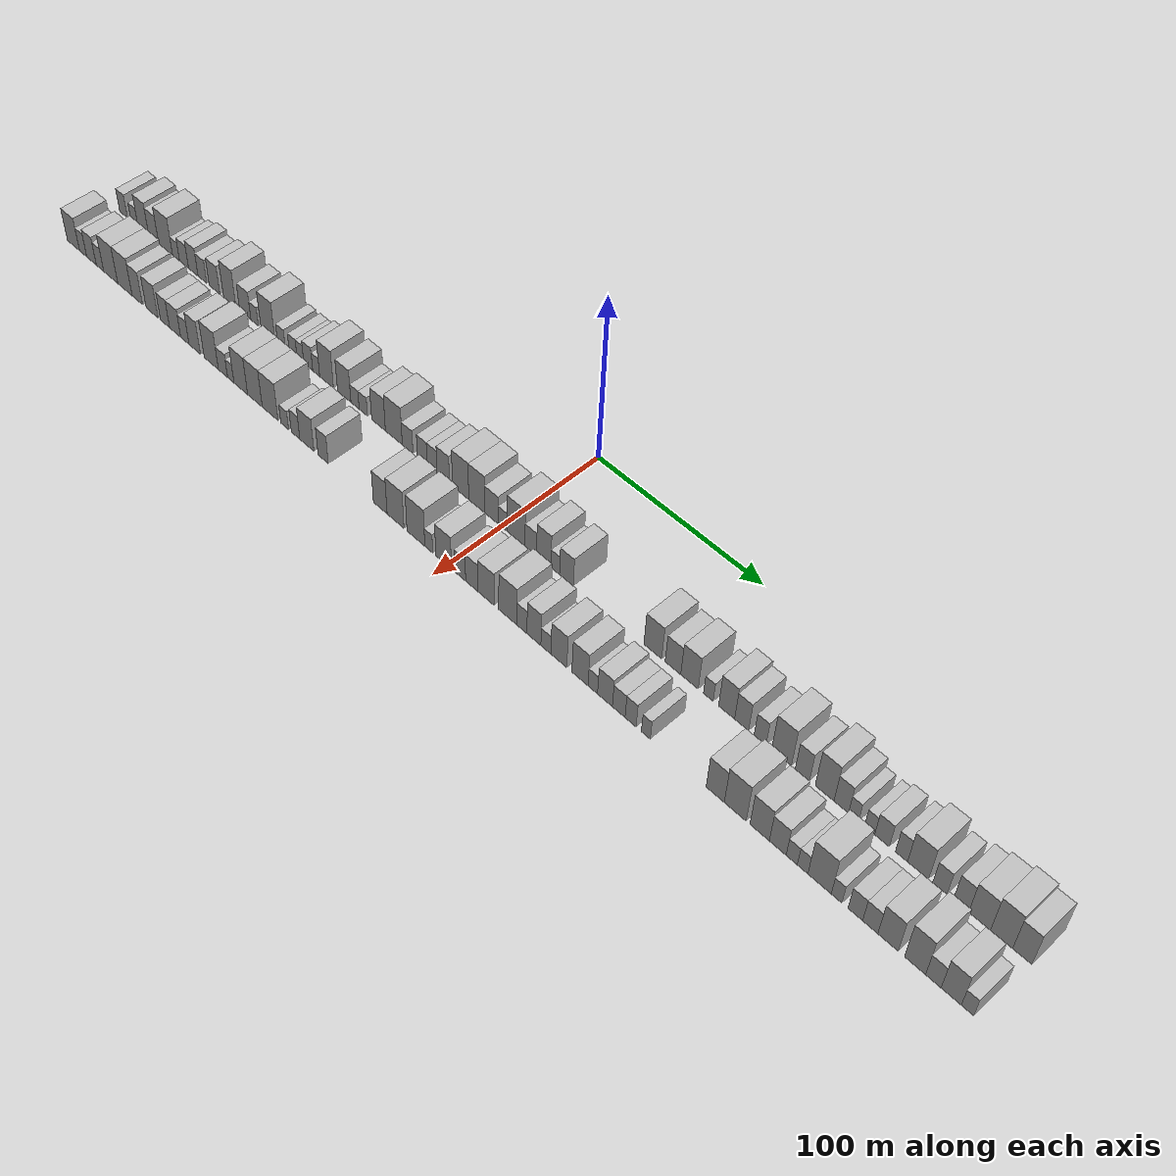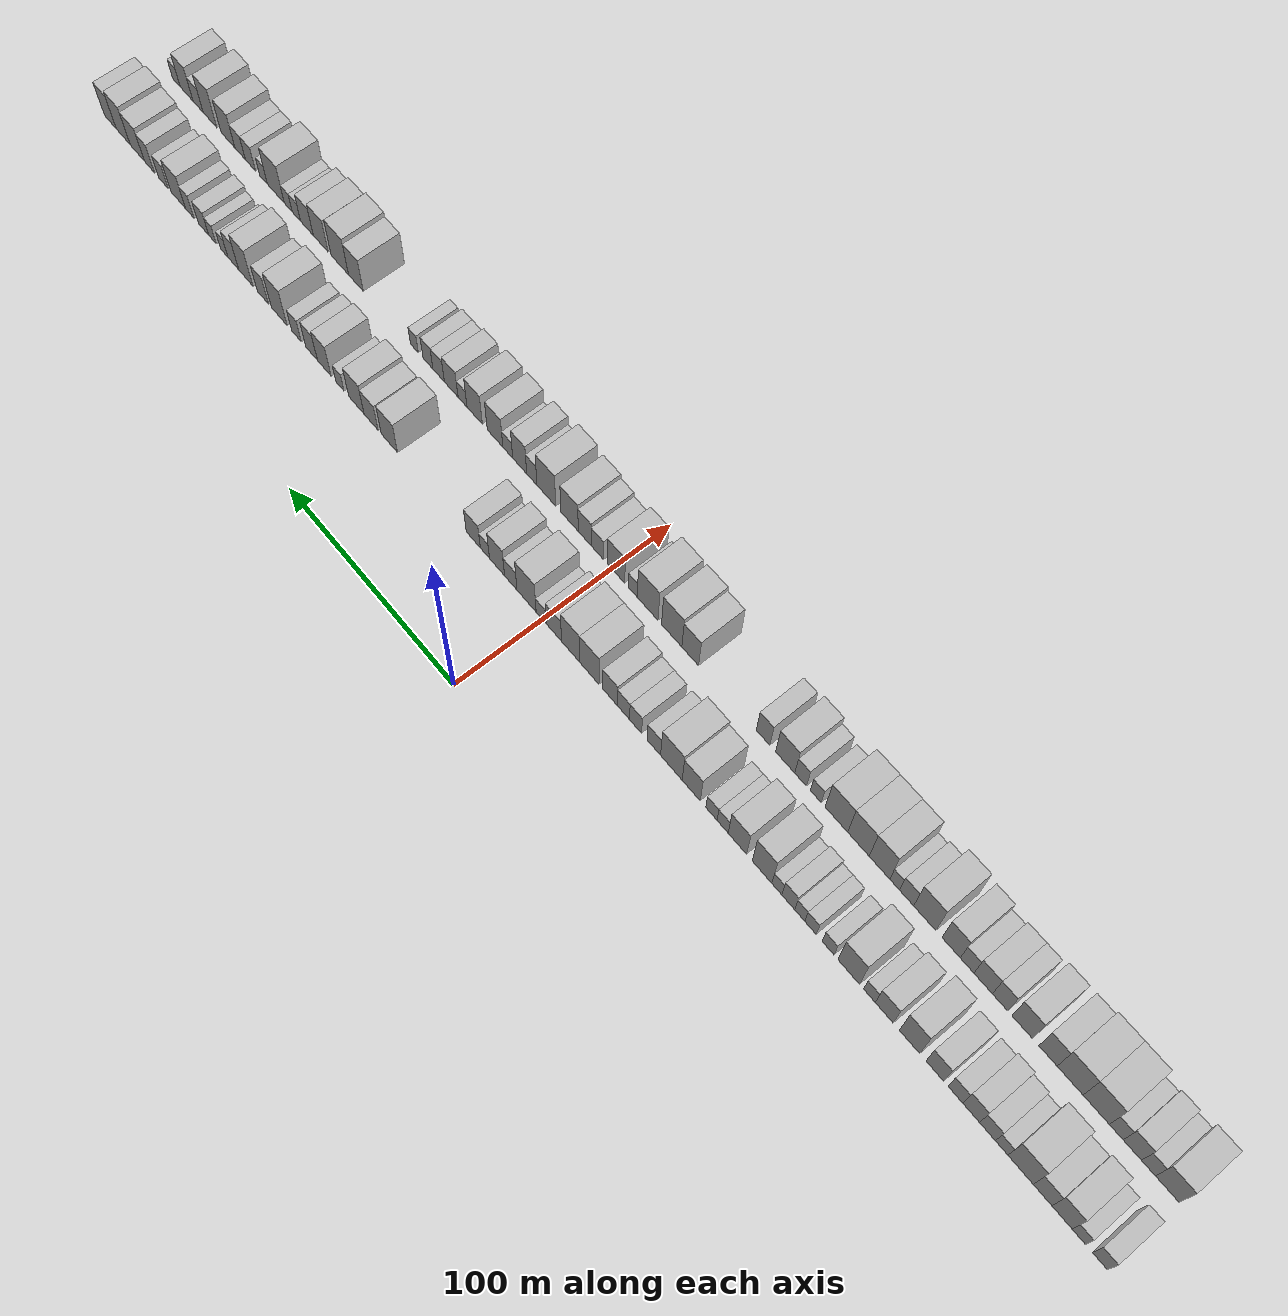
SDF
<sdf version="1.6">
 <world name="default">
  <scene>
   <sky><clouds><speed>12</speed></clouds></sky>
   <ambient>0.4 0.4 0.4 1</ambient>
   <background>0.7 0.7 0.7 1</background>
   <shadows>1</shadows>
  </scene>
  <gravity>0 0 -9.8066</gravity>
  <magnetic_field>6e-06 2.3e-05 -4.2e-05</magnetic_field>
  <physics default="0" name="default_physics" type="ode">
   <ode>
    <solver>
     <type>quick</type>
     <iters>10</iters>
     <sor>1.0</sor>
     <use_dynamic_moi_rescaling>0</use_dynamic_moi_rescaling>
    </solver>
    <constraints>
     <cfm>0</cfm>
     <erp>0.2</erp>
     <contact_max_correcting_vel>100</contact_max_correcting_vel>
     <contact_surface_layer>0.001</contact_surface_layer>
    </constraints>
   </ode>
   <max_step_size>0.004</max_step_size>
   <real_time_factor>1</real_time_factor>
   <real_time_update_rate>250</real_time_update_rate>
  </physics>
  <light name="sun" type="directional">
   <pose>0 0 10 0 0 0</pose>
   <diffuse>0.8 0.8 0.8 1</diffuse>
   <specular>0.2 0.2 0.2 1</specular>
   <attenuation>
    <range>1000</range>
    <constant>0.9</constant>
    <linear>0.01</linear>
    <quadratic>0.001</quadratic>
   </attenuation>
   <direction>-0.5 0.1 -0.9</direction>
  </light>
  <model name="building_1">
   <static>1</static>
   <pose>50.0000 -280.6989 0 0.000000 0.000000 0.000000</pose>
   <link name="link">
    <pose>0 0 7.50 0 0 0</pose>
    <collision name="collision"><geometry><box><size>20.0000 6.6021 15.0000</size></box></geometry></collision>
    <visual name="visual">
     <cast_shadows>0</cast_shadows>
     <geometry><box><size>20.0000 6.6021 15.0000</size></box></geometry>
     <material>
      <script>
       <uri>model://HANNAS_wall/materials/scripts</uri>
       <uri>model://HANNAS_wall/materials/textures</uri>
       <name>vrc/HANNAS_wall</name>
      </script>
     </material>
    </visual>
   </link>
  </model>
  <model name="building_2">
   <static>1</static>
   <pose>50.0000 -271.4203 0 0.000000 0.000000 0.000000</pose>
   <link name="link">
    <pose>0 0 6.00 0 0 0</pose>
    <collision name="collision"><geometry><box><size>20.0000 5.9551 12.0000</size></box></geometry></collision>
    <visual name="visual">
     <cast_shadows>0</cast_shadows>
     <geometry><box><size>20.0000 5.9551 12.0000</size></box></geometry>
     <material>
      <script>
       <uri>model://HANNAS_wall/materials/scripts</uri>
       <uri>model://HANNAS_wall/materials/textures</uri>
       <name>vrc/HANNAS_wall</name>
      </script>
     </material>
    </visual>
   </link>
  </model>
  <model name="building_3">
   <static>1</static>
   <pose>50.0000 -263.9315 0 0.000000 0.000000 0.000000</pose>
   <link name="link">
    <pose>0 0 10.50 0 0 0</pose>
    <collision name="collision"><geometry><box><size>20.0000 9.0226 21.0000</size></box></geometry></collision>
    <visual name="visual">
     <cast_shadows>0</cast_shadows>
     <geometry><box><size>20.0000 9.0226 21.0000</size></box></geometry>
     <material>
      <script>
       <uri>model://HANNAS_wall/materials/scripts</uri>
       <uri>model://HANNAS_wall/materials/textures</uri>
       <name>vrc/HANNAS_wall</name>
      </script>
     </material>
    </visual>
   </link>
  </model>
  <model name="building_4">
   <static>1</static>
   <pose>50.0000 -255.2241 0 0.000000 0.000000 0.000000</pose>
   <link name="link">
    <pose>0 0 9.00 0 0 0</pose>
    <collision name="collision"><geometry><box><size>20.0000 8.3921 18.0000</size></box></geometry></collision>
    <visual name="visual">
     <cast_shadows>0</cast_shadows>
     <geometry><box><size>20.0000 8.3921 18.0000</size></box></geometry>
     <material>
      <script>
       <uri>model://HANNAS_wall/materials/scripts</uri>
       <uri>model://HANNAS_wall/materials/textures</uri>
       <name>vrc/HANNAS_wall</name>
      </script>
     </material>
    </visual>
   </link>
  </model>
  <model name="building_5">
   <static>1</static>
   <pose>50.0000 -245.2907 0 0.000000 0.000000 0.000000</pose>
   <link name="link">
    <pose>0 0 12.00 0 0 0</pose>
    <collision name="collision"><geometry><box><size>20.0000 11.4748 24.0000</size></box></geometry></collision>
    <visual name="visual">
     <cast_shadows>0</cast_shadows>
     <geometry><box><size>20.0000 11.4748 24.0000</size></box></geometry>
     <material>
      <script>
       <uri>model://HANNAS_wall/materials/scripts</uri>
       <uri>model://HANNAS_wall/materials/textures</uri>
       <name>vrc/HANNAS_wall</name>
      </script>
     </material>
    </visual>
   </link>
  </model>
  <model name="building_6">
   <static>1</static>
   <pose>50.0000 -236.6807 0 0.000000 0.000000 0.000000</pose>
   <link name="link">
    <pose>0 0 6.00 0 0 0</pose>
    <collision name="collision"><geometry><box><size>20.0000 5.7452 12.0000</size></box></geometry></collision>
    <visual name="visual">
     <cast_shadows>0</cast_shadows>
     <geometry><box><size>20.0000 5.7452 12.0000</size></box></geometry>
     <material>
      <script>
       <uri>model://HANNAS_wall/materials/scripts</uri>
       <uri>model://HANNAS_wall/materials/textures</uri>
       <name>vrc/HANNAS_wall</name>
      </script>
     </material>
    </visual>
   </link>
  </model>
  <model name="building_7">
   <static>1</static>
   <pose>50.0000 -230.1523 0 0.000000 0.000000 0.000000</pose>
   <link name="link">
    <pose>0 0 7.50 0 0 0</pose>
    <collision name="collision"><geometry><box><size>20.0000 7.3116 15.0000</size></box></geometry></collision>
    <visual name="visual">
     <cast_shadows>0</cast_shadows>
     <geometry><box><size>20.0000 7.3116 15.0000</size></box></geometry>
     <material>
      <script>
       <uri>model://HANNAS_wall/materials/scripts</uri>
       <uri>model://HANNAS_wall/materials/textures</uri>
       <name>vrc/HANNAS_wall</name>
      </script>
     </material>
    </visual>
   </link>
  </model>
  <model name="building_8">
   <static>1</static>
   <pose>50.0000 -222.6213 0 0.000000 0.000000 0.000000</pose>
   <link name="link">
    <pose>0 0 9.00 0 0 0</pose>
    <collision name="collision"><geometry><box><size>20.0000 7.7506 18.0000</size></box></geometry></collision>
    <visual name="visual">
     <cast_shadows>0</cast_shadows>
     <geometry><box><size>20.0000 7.7506 18.0000</size></box></geometry>
     <material>
      <script>
       <uri>model://HANNAS_wall/materials/scripts</uri>
       <uri>model://HANNAS_wall/materials/textures</uri>
       <name>vrc/HANNAS_wall</name>
      </script>
     </material>
    </visual>
   </link>
  </model>
  <model name="building_9">
   <static>1</static>
   <pose>50.0000 -215.2409 0 0.000000 0.000000 0.000000</pose>
   <link name="link">
    <pose>0 0 7.50 0 0 0</pose>
    <collision name="collision"><geometry><box><size>20.0000 7.0102 15.0000</size></box></geometry></collision>
    <visual name="visual">
     <cast_shadows>0</cast_shadows>
     <geometry><box><size>20.0000 7.0102 15.0000</size></box></geometry>
     <material>
      <script>
       <uri>model://HANNAS_wall/materials/scripts</uri>
       <uri>model://HANNAS_wall/materials/textures</uri>
       <name>vrc/HANNAS_wall</name>
      </script>
     </material>
    </visual>
   </link>
  </model>
  <model name="building_10">
   <static>1</static>
   <pose>50.0000 -205.5315 0 0.000000 0.000000 0.000000</pose>
   <link name="link">
    <pose>0 0 9.00 0 0 0</pose>
    <collision name="collision"><geometry><box><size>20.0000 8.4085 18.0000</size></box></geometry></collision>
    <visual name="visual">
     <cast_shadows>0</cast_shadows>
     <geometry><box><size>20.0000 8.4085 18.0000</size></box></geometry>
     <material>
      <script>
       <uri>model://HANNAS_wall/materials/scripts</uri>
       <uri>model://HANNAS_wall/materials/textures</uri>
       <name>vrc/HANNAS_wall</name>
      </script>
     </material>
    </visual>
   </link>
  </model>
  <model name="building_11">
   <static>1</static>
   <pose>50.0000 -193.4577 0 0.000000 0.000000 0.000000</pose>
   <link name="link">
    <pose>0 0 12.00 0 0 0</pose>
    <collision name="collision"><geometry><box><size>20.0000 9.7391 24.0000</size></box></geometry></collision>
    <visual name="visual">
     <cast_shadows>0</cast_shadows>
     <geometry><box><size>20.0000 9.7391 24.0000</size></box></geometry>
     <material>
      <script>
       <uri>model://HANNAS_wall/materials/scripts</uri>
       <uri>model://HANNAS_wall/materials/textures</uri>
       <name>vrc/HANNAS_wall</name>
      </script>
     </material>
    </visual>
   </link>
  </model>
  <model name="building_12">
   <static>1</static>
   <pose>50.0000 -181.2519 0 0.000000 0.000000 0.000000</pose>
   <link name="link">
    <pose>0 0 9.00 0 0 0</pose>
    <collision name="collision"><geometry><box><size>20.0000 8.6725 18.0000</size></box></geometry></collision>
    <visual name="visual">
     <cast_shadows>0</cast_shadows>
     <geometry><box><size>20.0000 8.6725 18.0000</size></box></geometry>
     <material>
      <script>
       <uri>model://HANNAS_wall/materials/scripts</uri>
       <uri>model://HANNAS_wall/materials/textures</uri>
       <name>vrc/HANNAS_wall</name>
      </script>
     </material>
    </visual>
   </link>
  </model>
  <model name="building_13">
   <static>1</static>
   <pose>50.0000 -174.0403 0 0.000000 0.000000 0.000000</pose>
   <link name="link">
    <pose>0 0 6.00 0 0 0</pose>
    <collision name="collision"><geometry><box><size>20.0000 5.7507 12.0000</size></box></geometry></collision>
    <visual name="visual">
     <cast_shadows>0</cast_shadows>
     <geometry><box><size>20.0000 5.7507 12.0000</size></box></geometry>
     <material>
      <script>
       <uri>model://HANNAS_wall/materials/scripts</uri>
       <uri>model://HANNAS_wall/materials/textures</uri>
       <name>vrc/HANNAS_wall</name>
      </script>
     </material>
    </visual>
   </link>
  </model>
  <model name="building_14">
   <static>1</static>
   <pose>50.0000 -163.8417 0 0.000000 0.000000 0.000000</pose>
   <link name="link">
    <pose>0 0 12.00 0 0 0</pose>
    <collision name="collision"><geometry><box><size>20.0000 10.6465 24.0000</size></box></geometry></collision>
    <visual name="visual">
     <cast_shadows>0</cast_shadows>
     <geometry><box><size>20.0000 10.6465 24.0000</size></box></geometry>
     <material>
      <script>
       <uri>model://HANNAS_wall/materials/scripts</uri>
       <uri>model://HANNAS_wall/materials/textures</uri>
       <name>vrc/HANNAS_wall</name>
      </script>
     </material>
    </visual>
   </link>
  </model>
  <model name="building_15">
   <static>1</static>
   <pose>50.0000 -153.5660 0 0.000000 0.000000 0.000000</pose>
   <link name="link">
    <pose>0 0 6.00 0 0 0</pose>
    <collision name="collision"><geometry><box><size>20.0000 5.9048 12.0000</size></box></geometry></collision>
    <visual name="visual">
     <cast_shadows>0</cast_shadows>
     <geometry><box><size>20.0000 5.9048 12.0000</size></box></geometry>
     <material>
      <script>
       <uri>model://HANNAS_wall/materials/scripts</uri>
       <uri>model://HANNAS_wall/materials/textures</uri>
       <name>vrc/HANNAS_wall</name>
      </script>
     </material>
    </visual>
   </link>
  </model>
  <model name="building_16">
   <static>1</static>
   <pose>50.0000 -144.7277 0 0.000000 0.000000 0.000000</pose>
   <link name="link">
    <pose>0 0 6.00 0 0 0</pose>
    <collision name="collision"><geometry><box><size>20.0000 5.7719 12.0000</size></box></geometry></collision>
    <visual name="visual">
     <cast_shadows>0</cast_shadows>
     <geometry><box><size>20.0000 5.7719 12.0000</size></box></geometry>
     <material>
      <script>
       <uri>model://HANNAS_wall/materials/scripts</uri>
       <uri>model://HANNAS_wall/materials/textures</uri>
       <name>vrc/HANNAS_wall</name>
      </script>
     </material>
    </visual>
   </link>
  </model>
  <model name="building_17">
   <static>1</static>
   <pose>50.0000 -139.3136 0 0.000000 0.000000 0.000000</pose>
   <link name="link">
    <pose>0 0 6.00 0 0 0</pose>
    <collision name="collision"><geometry><box><size>20.0000 5.0563 12.0000</size></box></geometry></collision>
    <visual name="visual">
     <cast_shadows>0</cast_shadows>
     <geometry><box><size>20.0000 5.0563 12.0000</size></box></geometry>
     <material>
      <script>
       <uri>model://HANNAS_wall/materials/scripts</uri>
       <uri>model://HANNAS_wall/materials/textures</uri>
       <name>vrc/HANNAS_wall</name>
      </script>
     </material>
    </visual>
   </link>
  </model>
  <model name="building_18">
   <static>1</static>
   <pose>50.0000 -133.4792 0 0.000000 0.000000 0.000000</pose>
   <link name="link">
    <pose>0 0 7.50 0 0 0</pose>
    <collision name="collision"><geometry><box><size>20.0000 6.6124 15.0000</size></box></geometry></collision>
    <visual name="visual">
     <cast_shadows>0</cast_shadows>
     <geometry><box><size>20.0000 6.6124 15.0000</size></box></geometry>
     <material>
      <script>
       <uri>model://HANNAS_wall/materials/scripts</uri>
       <uri>model://HANNAS_wall/materials/textures</uri>
       <name>vrc/HANNAS_wall</name>
      </script>
     </material>
    </visual>
   </link>
  </model>
  <model name="building_19">
   <static>1</static>
   <pose>50.0000 -127.5917 0 0.000000 0.000000 0.000000</pose>
   <link name="link">
    <pose>0 0 6.00 0 0 0</pose>
    <collision name="collision"><geometry><box><size>20.0000 5.1625 12.0000</size></box></geometry></collision>
    <visual name="visual">
     <cast_shadows>0</cast_shadows>
     <geometry><box><size>20.0000 5.1625 12.0000</size></box></geometry>
     <material>
      <script>
       <uri>model://HANNAS_wall/materials/scripts</uri>
       <uri>model://HANNAS_wall/materials/textures</uri>
       <name>vrc/HANNAS_wall</name>
      </script>
     </material>
    </visual>
   </link>
  </model>
  <model name="building_20">
   <static>1</static>
   <pose>50.0000 -119.9798 0 0.000000 0.000000 0.000000</pose>
   <link name="link">
    <pose>0 0 12.00 0 0 0</pose>
    <collision name="collision"><geometry><box><size>20.0000 10.0615 24.0000</size></box></geometry></collision>
    <visual name="visual">
     <cast_shadows>0</cast_shadows>
     <geometry><box><size>20.0000 10.0615 24.0000</size></box></geometry>
     <material>
      <script>
       <uri>model://HANNAS_wall/materials/scripts</uri>
       <uri>model://HANNAS_wall/materials/textures</uri>
       <name>vrc/HANNAS_wall</name>
      </script>
     </material>
    </visual>
   </link>
  </model>
  <model name="building_21">
   <static>1</static>
   <pose>50.0000 -107.1472 0 0.000000 0.000000 0.000000</pose>
   <link name="link">
    <pose>0 0 10.50 0 0 0</pose>
    <collision name="collision"><geometry><box><size>20.0000 9.6036 21.0000</size></box></geometry></collision>
    <visual name="visual">
     <cast_shadows>0</cast_shadows>
     <geometry><box><size>20.0000 9.6036 21.0000</size></box></geometry>
     <material>
      <script>
       <uri>model://HANNAS_wall/materials/scripts</uri>
       <uri>model://HANNAS_wall/materials/textures</uri>
       <name>vrc/HANNAS_wall</name>
      </script>
     </material>
    </visual>
   </link>
  </model>
  <model name="building_22">
   <static>1</static>
   <pose>50.0000 -99.4069 0 0.000000 0.000000 0.000000</pose>
   <link name="link">
    <pose>0 0 6.00 0 0 0</pose>
    <collision name="collision"><geometry><box><size>20.0000 5.8770 12.0000</size></box></geometry></collision>
    <visual name="visual">
     <cast_shadows>0</cast_shadows>
     <geometry><box><size>20.0000 5.8770 12.0000</size></box></geometry>
     <material>
      <script>
       <uri>model://HANNAS_wall/materials/scripts</uri>
       <uri>model://HANNAS_wall/materials/textures</uri>
       <name>vrc/HANNAS_wall</name>
      </script>
     </material>
    </visual>
   </link>
  </model>
  <model name="building_23">
   <static>1</static>
   <pose>50.0000 -93.5156 0 0.000000 0.000000 0.000000</pose>
   <link name="link">
    <pose>0 0 6.00 0 0 0</pose>
    <collision name="collision"><geometry><box><size>20.0000 5.9058 12.0000</size></box></geometry></collision>
    <visual name="visual">
     <cast_shadows>0</cast_shadows>
     <geometry><box><size>20.0000 5.9058 12.0000</size></box></geometry>
     <material>
      <script>
       <uri>model://HANNAS_wall/materials/scripts</uri>
       <uri>model://HANNAS_wall/materials/textures</uri>
       <name>vrc/HANNAS_wall</name>
      </script>
     </material>
    </visual>
   </link>
  </model>
  <model name="building_24">
   <static>1</static>
   <pose>50.0000 -82.7268 0 0.000000 0.000000 0.000000</pose>
   <link name="link">
    <pose>0 0 10.50 0 0 0</pose>
    <collision name="collision"><geometry><box><size>20.0000 9.6717 21.0000</size></box></geometry></collision>
    <visual name="visual">
     <cast_shadows>0</cast_shadows>
     <geometry><box><size>20.0000 9.6717 21.0000</size></box></geometry>
     <material>
      <script>
       <uri>model://HANNAS_wall/materials/scripts</uri>
       <uri>model://HANNAS_wall/materials/textures</uri>
       <name>vrc/HANNAS_wall</name>
      </script>
     </material>
    </visual>
   </link>
  </model>
  <model name="building_25">
   <static>1</static>
   <pose>50.0000 -72.0523 0 0.000000 0.000000 0.000000</pose>
   <link name="link">
    <pose>0 0 12.00 0 0 0</pose>
    <collision name="collision"><geometry><box><size>20.0000 11.6772 24.0000</size></box></geometry></collision>
    <visual name="visual">
     <cast_shadows>0</cast_shadows>
     <geometry><box><size>20.0000 11.6772 24.0000</size></box></geometry>
     <material>
      <script>
       <uri>model://HANNAS_wall/materials/scripts</uri>
       <uri>model://HANNAS_wall/materials/textures</uri>
       <name>vrc/HANNAS_wall</name>
      </script>
     </material>
    </visual>
   </link>
  </model>
  <model name="building_26">
   <static>1</static>
   <pose>50.0000 -62.5154 0 0.000000 0.000000 0.000000</pose>
   <link name="link">
    <pose>0 0 7.50 0 0 0</pose>
    <collision name="collision"><geometry><box><size>20.0000 7.3966 15.0000</size></box></geometry></collision>
    <visual name="visual">
     <cast_shadows>0</cast_shadows>
     <geometry><box><size>20.0000 7.3966 15.0000</size></box></geometry>
     <material>
      <script>
       <uri>model://HANNAS_wall/materials/scripts</uri>
       <uri>model://HANNAS_wall/materials/textures</uri>
       <name>vrc/HANNAS_wall</name>
      </script>
     </material>
    </visual>
   </link>
  </model>
  <model name="building_27">
   <static>1</static>
   <pose>50.0000 -52.4960 0 0.000000 0.000000 0.000000</pose>
   <link name="link">
    <pose>0 0 7.50 0 0 0</pose>
    <collision name="collision"><geometry><box><size>20.0000 6.6422 15.0000</size></box></geometry></collision>
    <visual name="visual">
     <cast_shadows>0</cast_shadows>
     <geometry><box><size>20.0000 6.6422 15.0000</size></box></geometry>
     <material>
      <script>
       <uri>model://HANNAS_wall/materials/scripts</uri>
       <uri>model://HANNAS_wall/materials/textures</uri>
       <name>vrc/HANNAS_wall</name>
      </script>
     </material>
    </visual>
   </link>
  </model>
  <model name="building_28">
   <static>1</static>
   <pose>50.0000 -45.8515 0 0.000000 0.000000 0.000000</pose>
   <link name="link">
    <pose>0 0 7.50 0 0 0</pose>
    <collision name="collision"><geometry><box><size>20.0000 6.6469 15.0000</size></box></geometry></collision>
    <visual name="visual">
     <cast_shadows>0</cast_shadows>
     <geometry><box><size>20.0000 6.6469 15.0000</size></box></geometry>
     <material>
      <script>
       <uri>model://HANNAS_wall/materials/scripts</uri>
       <uri>model://HANNAS_wall/materials/textures</uri>
       <name>vrc/HANNAS_wall</name>
      </script>
     </material>
    </visual>
   </link>
  </model>
  <model name="building_29">
   <static>1</static>
   <pose>50.0000 -38.3712 0 0.000000 0.000000 0.000000</pose>
   <link name="link">
    <pose>0 0 9.00 0 0 0</pose>
    <collision name="collision"><geometry><box><size>20.0000 8.3137 18.0000</size></box></geometry></collision>
    <visual name="visual">
     <cast_shadows>0</cast_shadows>
     <geometry><box><size>20.0000 8.3137 18.0000</size></box></geometry>
     <material>
      <script>
       <uri>model://HANNAS_wall/materials/scripts</uri>
       <uri>model://HANNAS_wall/materials/textures</uri>
       <name>vrc/HANNAS_wall</name>
      </script>
     </material>
    </visual>
   </link>
  </model>
  <model name="building_30">
   <static>1</static>
   <pose>50.0000 -26.8099 0 0.000000 0.000000 0.000000</pose>
   <link name="link">
    <pose>0 0 12.00 0 0 0</pose>
    <collision name="collision"><geometry><box><size>20.0000 10.8089 24.0000</size></box></geometry></collision>
    <visual name="visual">
     <cast_shadows>0</cast_shadows>
     <geometry><box><size>20.0000 10.8089 24.0000</size></box></geometry>
     <material>
      <script>
       <uri>model://HANNAS_wall/materials/scripts</uri>
       <uri>model://HANNAS_wall/materials/textures</uri>
       <name>vrc/HANNAS_wall</name>
      </script>
     </material>
    </visual>
   </link>
  </model>
  <model name="building_31">
   <static>1</static>
   <pose>50.0000 -16.1698 0 0.000000 0.000000 0.000000</pose>
   <link name="link">
    <pose>0 0 12.00 0 0 0</pose>
    <collision name="collision"><geometry><box><size>20.0000 10.4713 24.0000</size></box></geometry></collision>
    <visual name="visual">
     <cast_shadows>0</cast_shadows>
     <geometry><box><size>20.0000 10.4713 24.0000</size></box></geometry>
     <material>
      <script>
       <uri>model://HANNAS_wall/materials/scripts</uri>
       <uri>model://HANNAS_wall/materials/textures</uri>
       <name>vrc/HANNAS_wall</name>
      </script>
     </material>
    </visual>
   </link>
  </model>
  <model name="building_32">
   <static>1</static>
   <pose>50.0000 -6.5407 0 0.000000 0.000000 0.000000</pose>
   <link name="link">
    <pose>0 0 9.00 0 0 0</pose>
    <collision name="collision"><geometry><box><size>20.0000 8.7869 18.0000</size></box></geometry></collision>
    <visual name="visual">
     <cast_shadows>0</cast_shadows>
     <geometry><box><size>20.0000 8.7869 18.0000</size></box></geometry>
     <material>
      <script>
       <uri>model://HANNAS_wall/materials/scripts</uri>
       <uri>model://HANNAS_wall/materials/textures</uri>
       <name>vrc/HANNAS_wall</name>
      </script>
     </material>
    </visual>
   </link>
  </model>
  <model name="building_33">
   <static>1</static>
   <pose>50.0000 0.7738 0 0.000000 0.000000 0.000000</pose>
   <link name="link">
    <pose>0 0 6.00 0 0 0</pose>
    <collision name="collision"><geometry><box><size>20.0000 5.8419 12.0000</size></box></geometry></collision>
    <visual name="visual">
     <cast_shadows>0</cast_shadows>
     <geometry><box><size>20.0000 5.8419 12.0000</size></box></geometry>
     <material>
      <script>
       <uri>model://HANNAS_wall/materials/scripts</uri>
       <uri>model://HANNAS_wall/materials/textures</uri>
       <name>vrc/HANNAS_wall</name>
      </script>
     </material>
    </visual>
   </link>
  </model>
  <model name="building_34">
   <static>1</static>
   <pose>50.0000 9.2958 0 0.000000 0.000000 0.000000</pose>
   <link name="link">
    <pose>0 0 12.00 0 0 0</pose>
    <collision name="collision"><geometry><box><size>20.0000 11.2023 24.0000</size></box></geometry></collision>
    <visual name="visual">
     <cast_shadows>0</cast_shadows>
     <geometry><box><size>20.0000 11.2023 24.0000</size></box></geometry>
     <material>
      <script>
       <uri>model://HANNAS_wall/materials/scripts</uri>
       <uri>model://HANNAS_wall/materials/textures</uri>
       <name>vrc/HANNAS_wall</name>
      </script>
     </material>
    </visual>
   </link>
  </model>
  <model name="building_35">
   <static>1</static>
   <pose>50.0000 18.5480 0 0.000000 0.000000 0.000000</pose>
   <link name="link">
    <pose>0 0 7.50 0 0 0</pose>
    <collision name="collision"><geometry><box><size>20.0000 7.3020 15.0000</size></box></geometry></collision>
    <visual name="visual">
     <cast_shadows>0</cast_shadows>
     <geometry><box><size>20.0000 7.3020 15.0000</size></box></geometry>
     <material>
      <script>
       <uri>model://HANNAS_wall/materials/scripts</uri>
       <uri>model://HANNAS_wall/materials/textures</uri>
       <name>vrc/HANNAS_wall</name>
      </script>
     </material>
    </visual>
   </link>
  </model>
  <model name="building_36">
   <static>1</static>
   <pose>50.0000 26.6706 0 0.000000 0.000000 0.000000</pose>
   <link name="link">
    <pose>0 0 10.50 0 0 0</pose>
    <collision name="collision"><geometry><box><size>20.0000 8.9432 21.0000</size></box></geometry></collision>
    <visual name="visual">
     <cast_shadows>0</cast_shadows>
     <geometry><box><size>20.0000 8.9432 21.0000</size></box></geometry>
     <material>
      <script>
       <uri>model://HANNAS_wall/materials/scripts</uri>
       <uri>model://HANNAS_wall/materials/textures</uri>
       <name>vrc/HANNAS_wall</name>
      </script>
     </material>
    </visual>
   </link>
  </model>
  <model name="building_37">
   <static>1</static>
   <pose>50.0000 33.8603 0 0.000000 0.000000 0.000000</pose>
   <link name="link">
    <pose>0 0 6.00 0 0 0</pose>
    <collision name="collision"><geometry><box><size>20.0000 5.4363 12.0000</size></box></geometry></collision>
    <visual name="visual">
     <cast_shadows>0</cast_shadows>
     <geometry><box><size>20.0000 5.4363 12.0000</size></box></geometry>
     <material>
      <script>
       <uri>model://HANNAS_wall/materials/scripts</uri>
       <uri>model://HANNAS_wall/materials/textures</uri>
       <name>vrc/HANNAS_wall</name>
      </script>
     </material>
    </visual>
   </link>
  </model>
  <model name="building_38">
   <static>1</static>
   <pose>50.0000 40.8012 0 0.000000 0.000000 0.000000</pose>
   <link name="link">
    <pose>0 0 9.00 0 0 0</pose>
    <collision name="collision"><geometry><box><size>20.0000 8.4455 18.0000</size></box></geometry></collision>
    <visual name="visual">
     <cast_shadows>0</cast_shadows>
     <geometry><box><size>20.0000 8.4455 18.0000</size></box></geometry>
     <material>
      <script>
       <uri>model://HANNAS_wall/materials/scripts</uri>
       <uri>model://HANNAS_wall/materials/textures</uri>
       <name>vrc/HANNAS_wall</name>
      </script>
     </material>
    </visual>
   </link>
  </model>
  <model name="building_39">
   <static>1</static>
   <pose>50.0000 92.3838 0 0.000000 0.000000 0.000000</pose>
   <link name="link">
    <pose>0 0 10.50 0 0 0</pose>
    <collision name="collision"><geometry><box><size>20.0000 10.2399 21.0000</size></box></geometry></collision>
    <visual name="visual">
     <cast_shadows>0</cast_shadows>
     <geometry><box><size>20.0000 10.2399 21.0000</size></box></geometry>
     <material>
      <script>
       <uri>model://HANNAS_wall/materials/scripts</uri>
       <uri>model://HANNAS_wall/materials/textures</uri>
       <name>vrc/HANNAS_wall</name>
      </script>
     </material>
    </visual>
   </link>
  </model>
  <model name="building_40">
   <static>1</static>
   <pose>50.0000 103.9644 0 0.000000 0.000000 0.000000</pose>
   <link name="link">
    <pose>0 0 9.00 0 0 0</pose>
    <collision name="collision"><geometry><box><size>20.0000 8.9212 18.0000</size></box></geometry></collision>
    <visual name="visual">
     <cast_shadows>0</cast_shadows>
     <geometry><box><size>20.0000 8.9212 18.0000</size></box></geometry>
     <material>
      <script>
       <uri>model://HANNAS_wall/materials/scripts</uri>
       <uri>model://HANNAS_wall/materials/textures</uri>
       <name>vrc/HANNAS_wall</name>
      </script>
     </material>
    </visual>
   </link>
  </model>
  <model name="building_41">
   <static>1</static>
   <pose>50.0000 113.3632 0 0.000000 0.000000 0.000000</pose>
   <link name="link">
    <pose>0 0 10.50 0 0 0</pose>
    <collision name="collision"><geometry><box><size>20.0000 9.8763 21.0000</size></box></geometry></collision>
    <visual name="visual">
     <cast_shadows>0</cast_shadows>
     <geometry><box><size>20.0000 9.8763 21.0000</size></box></geometry>
     <material>
      <script>
       <uri>model://HANNAS_wall/materials/scripts</uri>
       <uri>model://HANNAS_wall/materials/textures</uri>
       <name>vrc/HANNAS_wall</name>
      </script>
     </material>
    </visual>
   </link>
  </model>
  <model name="building_42">
   <static>1</static>
   <pose>50.0000 123.9783 0 0.000000 0.000000 0.000000</pose>
   <link name="link">
    <pose>0 0 6.00 0 0 0</pose>
    <collision name="collision"><geometry><box><size>20.0000 5.3540 12.0000</size></box></geometry></collision>
    <visual name="visual">
     <cast_shadows>0</cast_shadows>
     <geometry><box><size>20.0000 5.3540 12.0000</size></box></geometry>
     <material>
      <script>
       <uri>model://HANNAS_wall/materials/scripts</uri>
       <uri>model://HANNAS_wall/materials/textures</uri>
       <name>vrc/HANNAS_wall</name>
      </script>
     </material>
    </visual>
   </link>
  </model>
  <model name="building_43">
   <static>1</static>
   <pose>50.0000 134.0967 0 0.000000 0.000000 0.000000</pose>
   <link name="link">
    <pose>0 0 10.50 0 0 0</pose>
    <collision name="collision"><geometry><box><size>20.0000 8.8829 21.0000</size></box></geometry></collision>
    <visual name="visual">
     <cast_shadows>0</cast_shadows>
     <geometry><box><size>20.0000 8.8829 21.0000</size></box></geometry>
     <material>
      <script>
       <uri>model://HANNAS_wall/materials/scripts</uri>
       <uri>model://HANNAS_wall/materials/textures</uri>
       <name>vrc/HANNAS_wall</name>
      </script>
     </material>
    </visual>
   </link>
  </model>
  <model name="building_44">
   <static>1</static>
   <pose>50.0000 142.3680 0 0.000000 0.000000 0.000000</pose>
   <link name="link">
    <pose>0 0 9.00 0 0 0</pose>
    <collision name="collision"><geometry><box><size>20.0000 7.6595 18.0000</size></box></geometry></collision>
    <visual name="visual">
     <cast_shadows>0</cast_shadows>
     <geometry><box><size>20.0000 7.6595 18.0000</size></box></geometry>
     <material>
      <script>
       <uri>model://HANNAS_wall/materials/scripts</uri>
       <uri>model://HANNAS_wall/materials/textures</uri>
       <name>vrc/HANNAS_wall</name>
      </script>
     </material>
    </visual>
   </link>
  </model>
  <model name="building_45">
   <static>1</static>
   <pose>50.0000 152.4048 0 0.000000 0.000000 0.000000</pose>
   <link name="link">
    <pose>0 0 7.50 0 0 0</pose>
    <collision name="collision"><geometry><box><size>20.0000 6.4142 15.0000</size></box></geometry></collision>
    <visual name="visual">
     <cast_shadows>0</cast_shadows>
     <geometry><box><size>20.0000 6.4142 15.0000</size></box></geometry>
     <material>
      <script>
       <uri>model://HANNAS_wall/materials/scripts</uri>
       <uri>model://HANNAS_wall/materials/textures</uri>
       <name>vrc/HANNAS_wall</name>
      </script>
     </material>
    </visual>
   </link>
  </model>
  <model name="building_46">
   <static>1</static>
   <pose>50.0000 163.8818 0 0.000000 0.000000 0.000000</pose>
   <link name="link">
    <pose>0 0 12.00 0 0 0</pose>
    <collision name="collision"><geometry><box><size>20.0000 10.5398 24.0000</size></box></geometry></collision>
    <visual name="visual">
     <cast_shadows>0</cast_shadows>
     <geometry><box><size>20.0000 10.5398 24.0000</size></box></geometry>
     <material>
      <script>
       <uri>model://HANNAS_wall/materials/scripts</uri>
       <uri>model://HANNAS_wall/materials/textures</uri>
       <name>vrc/HANNAS_wall</name>
      </script>
     </material>
    </visual>
   </link>
  </model>
  <model name="building_47">
   <static>1</static>
   <pose>50.0000 174.8968 0 0.000000 0.000000 0.000000</pose>
   <link name="link">
    <pose>0 0 9.00 0 0 0</pose>
    <collision name="collision"><geometry><box><size>20.0000 7.4903 18.0000</size></box></geometry></collision>
    <visual name="visual">
     <cast_shadows>0</cast_shadows>
     <geometry><box><size>20.0000 7.4903 18.0000</size></box></geometry>
     <material>
      <script>
       <uri>model://HANNAS_wall/materials/scripts</uri>
       <uri>model://HANNAS_wall/materials/textures</uri>
       <name>vrc/HANNAS_wall</name>
      </script>
     </material>
    </visual>
   </link>
  </model>
  <model name="building_48">
   <static>1</static>
   <pose>50.0000 186.5020 0 0.000000 0.000000 0.000000</pose>
   <link name="link">
    <pose>0 0 12.00 0 0 0</pose>
    <collision name="collision"><geometry><box><size>20.0000 9.7200 24.0000</size></box></geometry></collision>
    <visual name="visual">
     <cast_shadows>0</cast_shadows>
     <geometry><box><size>20.0000 9.7200 24.0000</size></box></geometry>
     <material>
      <script>
       <uri>model://HANNAS_wall/materials/scripts</uri>
       <uri>model://HANNAS_wall/materials/textures</uri>
       <name>vrc/HANNAS_wall</name>
      </script>
     </material>
    </visual>
   </link>
  </model>
  <model name="building_49">
   <static>1</static>
   <pose>50.0000 195.0931 0 0.000000 0.000000 0.000000</pose>
   <link name="link">
    <pose>0 0 9.00 0 0 0</pose>
    <collision name="collision"><geometry><box><size>20.0000 7.4622 18.0000</size></box></geometry></collision>
    <visual name="visual">
     <cast_shadows>0</cast_shadows>
     <geometry><box><size>20.0000 7.4622 18.0000</size></box></geometry>
     <material>
      <script>
       <uri>model://HANNAS_wall/materials/scripts</uri>
       <uri>model://HANNAS_wall/materials/textures</uri>
       <name>vrc/HANNAS_wall</name>
      </script>
     </material>
    </visual>
   </link>
  </model>
  <model name="building_50">
   <static>1</static>
   <pose>50.0000 201.3708 0 0.000000 0.000000 0.000000</pose>
   <link name="link">
    <pose>0 0 6.00 0 0 0</pose>
    <collision name="collision"><geometry><box><size>20.0000 5.0933 12.0000</size></box></geometry></collision>
    <visual name="visual">
     <cast_shadows>0</cast_shadows>
     <geometry><box><size>20.0000 5.0933 12.0000</size></box></geometry>
     <material>
      <script>
       <uri>model://HANNAS_wall/materials/scripts</uri>
       <uri>model://HANNAS_wall/materials/textures</uri>
       <name>vrc/HANNAS_wall</name>
      </script>
     </material>
    </visual>
   </link>
  </model>
  <model name="building_51">
   <static>1</static>
   <pose>50.0000 209.4964 0 0.000000 0.000000 0.000000</pose>
   <link name="link">
    <pose>0 0 6.00 0 0 0</pose>
    <collision name="collision"><geometry><box><size>20.0000 5.1578 12.0000</size></box></geometry></collision>
    <visual name="visual">
     <cast_shadows>0</cast_shadows>
     <geometry><box><size>20.0000 5.1578 12.0000</size></box></geometry>
     <material>
      <script>
       <uri>model://HANNAS_wall/materials/scripts</uri>
       <uri>model://HANNAS_wall/materials/textures</uri>
       <name>vrc/HANNAS_wall</name>
      </script>
     </material>
    </visual>
   </link>
  </model>
  <model name="building_52">
   <static>1</static>
   <pose>50.0000 215.7255 0 0.000000 0.000000 0.000000</pose>
   <link name="link">
    <pose>0 0 7.50 0 0 0</pose>
    <collision name="collision"><geometry><box><size>20.0000 7.3004 15.0000</size></box></geometry></collision>
    <visual name="visual">
     <cast_shadows>0</cast_shadows>
     <geometry><box><size>20.0000 7.3004 15.0000</size></box></geometry>
     <material>
      <script>
       <uri>model://HANNAS_wall/materials/scripts</uri>
       <uri>model://HANNAS_wall/materials/textures</uri>
       <name>vrc/HANNAS_wall</name>
      </script>
     </material>
    </visual>
   </link>
  </model>
  <model name="building_53">
   <static>1</static>
   <pose>50.0000 225.3765 0 0.000000 0.000000 0.000000</pose>
   <link name="link">
    <pose>0 0 7.50 0 0 0</pose>
    <collision name="collision"><geometry><box><size>20.0000 6.0014 15.0000</size></box></geometry></collision>
    <visual name="visual">
     <cast_shadows>0</cast_shadows>
     <geometry><box><size>20.0000 6.0014 15.0000</size></box></geometry>
     <material>
      <script>
       <uri>model://HANNAS_wall/materials/scripts</uri>
       <uri>model://HANNAS_wall/materials/textures</uri>
       <name>vrc/HANNAS_wall</name>
      </script>
     </material>
    </visual>
   </link>
  </model>
  <model name="building_54">
   <static>1</static>
   <pose>50.0000 233.5228 0 0.000000 0.000000 0.000000</pose>
   <link name="link">
    <pose>0 0 10.50 0 0 0</pose>
    <collision name="collision"><geometry><box><size>20.0000 10.2913 21.0000</size></box></geometry></collision>
    <visual name="visual">
     <cast_shadows>0</cast_shadows>
     <geometry><box><size>20.0000 10.2913 21.0000</size></box></geometry>
     <material>
      <script>
       <uri>model://HANNAS_wall/materials/scripts</uri>
       <uri>model://HANNAS_wall/materials/textures</uri>
       <name>vrc/HANNAS_wall</name>
      </script>
     </material>
    </visual>
   </link>
  </model>
  <model name="building_55">
   <static>1</static>
   <pose>50.0000 244.1194 0 0.000000 0.000000 0.000000</pose>
   <link name="link">
    <pose>0 0 7.50 0 0 0</pose>
    <collision name="collision"><geometry><box><size>20.0000 6.9017 15.0000</size></box></geometry></collision>
    <visual name="visual">
     <cast_shadows>0</cast_shadows>
     <geometry><box><size>20.0000 6.9017 15.0000</size></box></geometry>
     <material>
      <script>
       <uri>model://HANNAS_wall/materials/scripts</uri>
       <uri>model://HANNAS_wall/materials/textures</uri>
       <name>vrc/HANNAS_wall</name>
      </script>
     </material>
    </visual>
   </link>
  </model>
  <model name="building_56">
   <static>1</static>
   <pose>50.0000 254.2113 0 0.000000 0.000000 0.000000</pose>
   <link name="link">
    <pose>0 0 9.00 0 0 0</pose>
    <collision name="collision"><geometry><box><size>20.0000 7.2821 18.0000</size></box></geometry></collision>
    <visual name="visual">
     <cast_shadows>0</cast_shadows>
     <geometry><box><size>20.0000 7.2821 18.0000</size></box></geometry>
     <material>
      <script>
       <uri>model://HANNAS_wall/materials/scripts</uri>
       <uri>model://HANNAS_wall/materials/textures</uri>
       <name>vrc/HANNAS_wall</name>
      </script>
     </material>
    </visual>
   </link>
  </model>
  <model name="building_57">
   <static>1</static>
   <pose>50.0000 263.0016 0 0.000000 0.000000 0.000000</pose>
   <link name="link">
    <pose>0 0 10.50 0 0 0</pose>
    <collision name="collision"><geometry><box><size>20.0000 10.2986 21.0000</size></box></geometry></collision>
    <visual name="visual">
     <cast_shadows>0</cast_shadows>
     <geometry><box><size>20.0000 10.2986 21.0000</size></box></geometry>
     <material>
      <script>
       <uri>model://HANNAS_wall/materials/scripts</uri>
       <uri>model://HANNAS_wall/materials/textures</uri>
       <name>vrc/HANNAS_wall</name>
      </script>
     </material>
    </visual>
   </link>
  </model>
  <model name="building_58">
   <static>1</static>
   <pose>50.0000 273.3004 0 0.000000 0.000000 0.000000</pose>
   <link name="link">
    <pose>0 0 12.00 0 0 0</pose>
    <collision name="collision"><geometry><box><size>20.0000 10.2991 24.0000</size></box></geometry></collision>
    <visual name="visual">
     <cast_shadows>0</cast_shadows>
     <geometry><box><size>20.0000 10.2991 24.0000</size></box></geometry>
     <material>
      <script>
       <uri>model://HANNAS_wall/materials/scripts</uri>
       <uri>model://HANNAS_wall/materials/textures</uri>
       <name>vrc/HANNAS_wall</name>
      </script>
     </material>
    </visual>
   </link>
  </model>
  <model name="building_59">
   <static>1</static>
   <pose>50.0000 282.8571 0 0.000000 0.000000 0.000000</pose>
   <link name="link">
    <pose>0 0 10.50 0 0 0</pose>
    <collision name="collision"><geometry><box><size>20.0000 8.8142 21.0000</size></box></geometry></collision>
    <visual name="visual">
     <cast_shadows>0</cast_shadows>
     <geometry><box><size>20.0000 8.8142 21.0000</size></box></geometry>
     <material>
      <script>
       <uri>model://HANNAS_wall/materials/scripts</uri>
       <uri>model://HANNAS_wall/materials/textures</uri>
       <name>vrc/HANNAS_wall</name>
      </script>
     </material>
    </visual>
   </link>
  </model>
  <model name="building_60">
   <static>1</static>
   <pose>82.0000 -278.7979 0 0.000000 0.000000 0.000000</pose>
   <link name="link">
    <pose>0 0 10.50 0 0 0</pose>
    <collision name="collision"><geometry><box><size>20.0000 10.4042 21.0000</size></box></geometry></collision>
    <visual name="visual">
     <cast_shadows>0</cast_shadows>
     <geometry><box><size>20.0000 10.4042 21.0000</size></box></geometry>
     <material>
      <script>
       <uri>model://HANNAS_wall/materials/scripts</uri>
       <uri>model://HANNAS_wall/materials/textures</uri>
       <name>vrc/HANNAS_wall</name>
      </script>
     </material>
    </visual>
   </link>
  </model>
  <model name="building_61">
   <static>1</static>
   <pose>82.0000 -270.5188 0 0.000000 0.000000 0.000000</pose>
   <link name="link">
    <pose>0 0 7.50 0 0 0</pose>
    <collision name="collision"><geometry><box><size>20.0000 6.1541 15.0000</size></box></geometry></collision>
    <visual name="visual">
     <cast_shadows>0</cast_shadows>
     <geometry><box><size>20.0000 6.1541 15.0000</size></box></geometry>
     <material>
      <script>
       <uri>model://HANNAS_wall/materials/scripts</uri>
       <uri>model://HANNAS_wall/materials/textures</uri>
       <name>vrc/HANNAS_wall</name>
      </script>
     </material>
    </visual>
   </link>
  </model>
  <model name="building_62">
   <static>1</static>
   <pose>82.0000 -263.3850 0 0.000000 0.000000 0.000000</pose>
   <link name="link">
    <pose>0 0 9.00 0 0 0</pose>
    <collision name="collision"><geometry><box><size>20.0000 8.1135 18.0000</size></box></geometry></collision>
    <visual name="visual">
     <cast_shadows>0</cast_shadows>
     <geometry><box><size>20.0000 8.1135 18.0000</size></box></geometry>
     <material>
      <script>
       <uri>model://HANNAS_wall/materials/scripts</uri>
       <uri>model://HANNAS_wall/materials/textures</uri>
       <name>vrc/HANNAS_wall</name>
      </script>
     </material>
    </visual>
   </link>
  </model>
  <model name="building_63">
   <static>1</static>
   <pose>82.0000 -256.2146 0 0.000000 0.000000 0.000000</pose>
   <link name="link">
    <pose>0 0 7.50 0 0 0</pose>
    <collision name="collision"><geometry><box><size>20.0000 6.2274 15.0000</size></box></geometry></collision>
    <visual name="visual">
     <cast_shadows>0</cast_shadows>
     <geometry><box><size>20.0000 6.2274 15.0000</size></box></geometry>
     <material>
      <script>
       <uri>model://HANNAS_wall/materials/scripts</uri>
       <uri>model://HANNAS_wall/materials/textures</uri>
       <name>vrc/HANNAS_wall</name>
      </script>
     </material>
    </visual>
   </link>
  </model>
  <model name="building_64">
   <static>1</static>
   <pose>82.0000 -247.1784 0 0.000000 0.000000 0.000000</pose>
   <link name="link">
    <pose>0 0 12.00 0 0 0</pose>
    <collision name="collision"><geometry><box><size>20.0000 11.8451 24.0000</size></box></geometry></collision>
    <visual name="visual">
     <cast_shadows>0</cast_shadows>
     <geometry><box><size>20.0000 11.8451 24.0000</size></box></geometry>
     <material>
      <script>
       <uri>model://HANNAS_wall/materials/scripts</uri>
       <uri>model://HANNAS_wall/materials/textures</uri>
       <name>vrc/HANNAS_wall</name>
      </script>
     </material>
    </visual>
   </link>
  </model>
  <model name="building_65">
   <static>1</static>
   <pose>82.0000 -235.3333 0 0.000000 0.000000 0.000000</pose>
   <link name="link">
    <pose>0 0 12.00 0 0 0</pose>
    <collision name="collision"><geometry><box><size>20.0000 11.8450 24.0000</size></box></geometry></collision>
    <visual name="visual">
     <cast_shadows>0</cast_shadows>
     <geometry><box><size>20.0000 11.8450 24.0000</size></box></geometry>
     <material>
      <script>
       <uri>model://HANNAS_wall/materials/scripts</uri>
       <uri>model://HANNAS_wall/materials/textures</uri>
       <name>vrc/HANNAS_wall</name>
      </script>
     </material>
    </visual>
   </link>
  </model>
  <model name="building_66">
   <static>1</static>
   <pose>82.0000 -225.1720 0 0.000000 0.000000 0.000000</pose>
   <link name="link">
    <pose>0 0 10.50 0 0 0</pose>
    <collision name="collision"><geometry><box><size>20.0000 8.4777 21.0000</size></box></geometry></collision>
    <visual name="visual">
     <cast_shadows>0</cast_shadows>
     <geometry><box><size>20.0000 8.4777 21.0000</size></box></geometry>
     <material>
      <script>
       <uri>model://HANNAS_wall/materials/scripts</uri>
       <uri>model://HANNAS_wall/materials/textures</uri>
       <name>vrc/HANNAS_wall</name>
      </script>
     </material>
    </visual>
   </link>
  </model>
  <model name="building_67">
   <static>1</static>
   <pose>82.0000 -213.1423 0 0.000000 0.000000 0.000000</pose>
   <link name="link">
    <pose>0 0 10.50 0 0 0</pose>
    <collision name="collision"><geometry><box><size>20.0000 9.5817 21.0000</size></box></geometry></collision>
    <visual name="visual">
     <cast_shadows>0</cast_shadows>
     <geometry><box><size>20.0000 9.5817 21.0000</size></box></geometry>
     <material>
      <script>
       <uri>model://HANNAS_wall/materials/scripts</uri>
       <uri>model://HANNAS_wall/materials/textures</uri>
       <name>vrc/HANNAS_wall</name>
      </script>
     </material>
    </visual>
   </link>
  </model>
  <model name="building_68">
   <static>1</static>
   <pose>82.0000 -202.7256 0 0.000000 0.000000 0.000000</pose>
   <link name="link">
    <pose>0 0 9.00 0 0 0</pose>
    <collision name="collision"><geometry><box><size>20.0000 7.2518 18.0000</size></box></geometry></collision>
    <visual name="visual">
     <cast_shadows>0</cast_shadows>
     <geometry><box><size>20.0000 7.2518 18.0000</size></box></geometry>
     <material>
      <script>
       <uri>model://HANNAS_wall/materials/scripts</uri>
       <uri>model://HANNAS_wall/materials/textures</uri>
       <name>vrc/HANNAS_wall</name>
      </script>
     </material>
    </visual>
   </link>
  </model>
  <model name="building_69">
   <static>1</static>
   <pose>82.0000 -194.6922 0 0.000000 0.000000 0.000000</pose>
   <link name="link">
    <pose>0 0 9.00 0 0 0</pose>
    <collision name="collision"><geometry><box><size>20.0000 8.8149 18.0000</size></box></geometry></collision>
    <visual name="visual">
     <cast_shadows>0</cast_shadows>
     <geometry><box><size>20.0000 8.8149 18.0000</size></box></geometry>
     <material>
      <script>
       <uri>model://HANNAS_wall/materials/scripts</uri>
       <uri>model://HANNAS_wall/materials/textures</uri>
       <name>vrc/HANNAS_wall</name>
      </script>
     </material>
    </visual>
   </link>
  </model>
  <model name="building_70">
   <static>1</static>
   <pose>82.0000 -187.0062 0 0.000000 0.000000 0.000000</pose>
   <link name="link">
    <pose>0 0 7.50 0 0 0</pose>
    <collision name="collision"><geometry><box><size>20.0000 6.5570 15.0000</size></box></geometry></collision>
    <visual name="visual">
     <cast_shadows>0</cast_shadows>
     <geometry><box><size>20.0000 6.5570 15.0000</size></box></geometry>
     <material>
      <script>
       <uri>model://HANNAS_wall/materials/scripts</uri>
       <uri>model://HANNAS_wall/materials/textures</uri>
       <name>vrc/HANNAS_wall</name>
      </script>
     </material>
    </visual>
   </link>
  </model>
  <model name="building_71">
   <static>1</static>
   <pose>82.0000 -179.2929 0 0.000000 0.000000 0.000000</pose>
   <link name="link">
    <pose>0 0 10.50 0 0 0</pose>
    <collision name="collision"><geometry><box><size>20.0000 8.8696 21.0000</size></box></geometry></collision>
    <visual name="visual">
     <cast_shadows>0</cast_shadows>
     <geometry><box><size>20.0000 8.8696 21.0000</size></box></geometry>
     <material>
      <script>
       <uri>model://HANNAS_wall/materials/scripts</uri>
       <uri>model://HANNAS_wall/materials/textures</uri>
       <name>vrc/HANNAS_wall</name>
      </script>
     </material>
    </visual>
   </link>
  </model>
  <model name="building_72">
   <static>1</static>
   <pose>82.0000 -166.4090 0 0.000000 0.000000 0.000000</pose>
   <link name="link">
    <pose>0 0 12.00 0 0 0</pose>
    <collision name="collision"><geometry><box><size>20.0000 10.8983 24.0000</size></box></geometry></collision>
    <visual name="visual">
     <cast_shadows>0</cast_shadows>
     <geometry><box><size>20.0000 10.8983 24.0000</size></box></geometry>
     <material>
      <script>
       <uri>model://HANNAS_wall/materials/scripts</uri>
       <uri>model://HANNAS_wall/materials/textures</uri>
       <name>vrc/HANNAS_wall</name>
      </script>
     </material>
    </visual>
   </link>
  </model>
  <model name="building_73">
   <static>1</static>
   <pose>82.0000 -157.4553 0 0.000000 0.000000 0.000000</pose>
   <link name="link">
    <pose>0 0 7.50 0 0 0</pose>
    <collision name="collision"><geometry><box><size>20.0000 7.0091 15.0000</size></box></geometry></collision>
    <visual name="visual">
     <cast_shadows>0</cast_shadows>
     <geometry><box><size>20.0000 7.0091 15.0000</size></box></geometry>
     <material>
      <script>
       <uri>model://HANNAS_wall/materials/scripts</uri>
       <uri>model://HANNAS_wall/materials/textures</uri>
       <name>vrc/HANNAS_wall</name>
      </script>
     </material>
    </visual>
   </link>
  </model>
  <model name="building_74">
   <static>1</static>
   <pose>82.0000 -151.5237 0 0.000000 0.000000 0.000000</pose>
   <link name="link">
    <pose>0 0 6.00 0 0 0</pose>
    <collision name="collision"><geometry><box><size>20.0000 4.8541 12.0000</size></box></geometry></collision>
    <visual name="visual">
     <cast_shadows>0</cast_shadows>
     <geometry><box><size>20.0000 4.8541 12.0000</size></box></geometry>
     <material>
      <script>
       <uri>model://HANNAS_wall/materials/scripts</uri>
       <uri>model://HANNAS_wall/materials/textures</uri>
       <name>vrc/HANNAS_wall</name>
      </script>
     </material>
    </visual>
   </link>
  </model>
  <model name="building_75">
   <static>1</static>
   <pose>82.0000 -143.9487 0 0.000000 0.000000 0.000000</pose>
   <link name="link">
    <pose>0 0 12.00 0 0 0</pose>
    <collision name="collision"><geometry><box><size>20.0000 10.2959 24.0000</size></box></geometry></collision>
    <visual name="visual">
     <cast_shadows>0</cast_shadows>
     <geometry><box><size>20.0000 10.2959 24.0000</size></box></geometry>
     <material>
      <script>
       <uri>model://HANNAS_wall/materials/scripts</uri>
       <uri>model://HANNAS_wall/materials/textures</uri>
       <name>vrc/HANNAS_wall</name>
      </script>
     </material>
    </visual>
   </link>
  </model>
  <model name="building_76">
   <static>1</static>
   <pose>82.0000 -133.3387 0 0.000000 0.000000 0.000000</pose>
   <link name="link">
    <pose>0 0 12.00 0 0 0</pose>
    <collision name="collision"><geometry><box><size>20.0000 10.9241 24.0000</size></box></geometry></collision>
    <visual name="visual">
     <cast_shadows>0</cast_shadows>
     <geometry><box><size>20.0000 10.9241 24.0000</size></box></geometry>
     <material>
      <script>
       <uri>model://HANNAS_wall/materials/scripts</uri>
       <uri>model://HANNAS_wall/materials/textures</uri>
       <name>vrc/HANNAS_wall</name>
      </script>
     </material>
    </visual>
   </link>
  </model>
  <model name="building_77">
   <static>1</static>
   <pose>82.0000 -122.0823 0 0.000000 0.000000 0.000000</pose>
   <link name="link">
    <pose>0 0 12.00 0 0 0</pose>
    <collision name="collision"><geometry><box><size>20.0000 11.5886 24.0000</size></box></geometry></collision>
    <visual name="visual">
     <cast_shadows>0</cast_shadows>
     <geometry><box><size>20.0000 11.5886 24.0000</size></box></geometry>
     <material>
      <script>
       <uri>model://HANNAS_wall/materials/scripts</uri>
       <uri>model://HANNAS_wall/materials/textures</uri>
       <name>vrc/HANNAS_wall</name>
      </script>
     </material>
    </visual>
   </link>
  </model>
  <model name="building_78">
   <static>1</static>
   <pose>82.0000 -111.4447 0 0.000000 0.000000 0.000000</pose>
   <link name="link">
    <pose>0 0 6.00 0 0 0</pose>
    <collision name="collision"><geometry><box><size>20.0000 5.6868 12.0000</size></box></geometry></collision>
    <visual name="visual">
     <cast_shadows>0</cast_shadows>
     <geometry><box><size>20.0000 5.6868 12.0000</size></box></geometry>
     <material>
      <script>
       <uri>model://HANNAS_wall/materials/scripts</uri>
       <uri>model://HANNAS_wall/materials/textures</uri>
       <name>vrc/HANNAS_wall</name>
      </script>
     </material>
    </visual>
   </link>
  </model>
  <model name="building_79">
   <static>1</static>
   <pose>82.0000 -103.5504 0 0.000000 0.000000 0.000000</pose>
   <link name="link">
    <pose>0 0 7.50 0 0 0</pose>
    <collision name="collision"><geometry><box><size>20.0000 6.1018 15.0000</size></box></geometry></collision>
    <visual name="visual">
     <cast_shadows>0</cast_shadows>
     <geometry><box><size>20.0000 6.1018 15.0000</size></box></geometry>
     <material>
      <script>
       <uri>model://HANNAS_wall/materials/scripts</uri>
       <uri>model://HANNAS_wall/materials/textures</uri>
       <name>vrc/HANNAS_wall</name>
      </script>
     </material>
    </visual>
   </link>
  </model>
  <model name="building_80">
   <static>1</static>
   <pose>82.0000 -95.4475 0 0.000000 0.000000 0.000000</pose>
   <link name="link">
    <pose>0 0 10.50 0 0 0</pose>
    <collision name="collision"><geometry><box><size>20.0000 10.1040 21.0000</size></box></geometry></collision>
    <visual name="visual">
     <cast_shadows>0</cast_shadows>
     <geometry><box><size>20.0000 10.1040 21.0000</size></box></geometry>
     <material>
      <script>
       <uri>model://HANNAS_wall/materials/scripts</uri>
       <uri>model://HANNAS_wall/materials/textures</uri>
       <name>vrc/HANNAS_wall</name>
      </script>
     </material>
    </visual>
   </link>
  </model>
  <model name="building_81">
   <static>1</static>
   <pose>82.0000 -83.7931 0 0.000000 0.000000 0.000000</pose>
   <link name="link">
    <pose>0 0 9.00 0 0 0</pose>
    <collision name="collision"><geometry><box><size>20.0000 7.2047 18.0000</size></box></geometry></collision>
    <visual name="visual">
     <cast_shadows>0</cast_shadows>
     <geometry><box><size>20.0000 7.2047 18.0000</size></box></geometry>
     <material>
      <script>
       <uri>model://HANNAS_wall/materials/scripts</uri>
       <uri>model://HANNAS_wall/materials/textures</uri>
       <name>vrc/HANNAS_wall</name>
      </script>
     </material>
    </visual>
   </link>
  </model>
  <model name="building_82">
   <static>1</static>
   <pose>82.0000 -44.2752 0 0.000000 0.000000 0.000000</pose>
   <link name="link">
    <pose>0 0 10.50 0 0 0</pose>
    <collision name="collision"><geometry><box><size>20.0000 9.2770 21.0000</size></box></geometry></collision>
    <visual name="visual">
     <cast_shadows>0</cast_shadows>
     <geometry><box><size>20.0000 9.2770 21.0000</size></box></geometry>
     <material>
      <script>
       <uri>model://HANNAS_wall/materials/scripts</uri>
       <uri>model://HANNAS_wall/materials/textures</uri>
       <name>vrc/HANNAS_wall</name>
      </script>
     </material>
    </visual>
   </link>
  </model>
  <model name="building_83">
   <static>1</static>
   <pose>82.0000 -33.9965 0 0.000000 0.000000 0.000000</pose>
   <link name="link">
    <pose>0 0 12.00 0 0 0</pose>
    <collision name="collision"><geometry><box><size>20.0000 11.2805 24.0000</size></box></geometry></collision>
    <visual name="visual">
     <cast_shadows>0</cast_shadows>
     <geometry><box><size>20.0000 11.2805 24.0000</size></box></geometry>
     <material>
      <script>
       <uri>model://HANNAS_wall/materials/scripts</uri>
       <uri>model://HANNAS_wall/materials/textures</uri>
       <name>vrc/HANNAS_wall</name>
      </script>
     </material>
    </visual>
   </link>
  </model>
  <model name="building_84">
   <static>1</static>
   <pose>82.0000 -20.4805 0 0.000000 0.000000 0.000000</pose>
   <link name="link">
    <pose>0 0 12.00 0 0 0</pose>
    <collision name="collision"><geometry><box><size>20.0000 11.7514 24.0000</size></box></geometry></collision>
    <visual name="visual">
     <cast_shadows>0</cast_shadows>
     <geometry><box><size>20.0000 11.7514 24.0000</size></box></geometry>
     <material>
      <script>
       <uri>model://HANNAS_wall/materials/scripts</uri>
       <uri>model://HANNAS_wall/materials/textures</uri>
       <name>vrc/HANNAS_wall</name>
      </script>
     </material>
    </visual>
   </link>
  </model>
  <model name="building_85">
   <static>1</static>
   <pose>82.0000 -12.0353 0 0.000000 0.000000 0.000000</pose>
   <link name="link">
    <pose>0 0 6.00 0 0 0</pose>
    <collision name="collision"><geometry><box><size>20.0000 5.1391 12.0000</size></box></geometry></collision>
    <visual name="visual">
     <cast_shadows>0</cast_shadows>
     <geometry><box><size>20.0000 5.1391 12.0000</size></box></geometry>
     <material>
      <script>
       <uri>model://HANNAS_wall/materials/scripts</uri>
       <uri>model://HANNAS_wall/materials/textures</uri>
       <name>vrc/HANNAS_wall</name>
      </script>
     </material>
    </visual>
   </link>
  </model>
  <model name="building_86">
   <static>1</static>
   <pose>82.0000 -2.4315 0 0.000000 0.000000 0.000000</pose>
   <link name="link">
    <pose>0 0 10.50 0 0 0</pose>
    <collision name="collision"><geometry><box><size>20.0000 10.0685 21.0000</size></box></geometry></collision>
    <visual name="visual">
     <cast_shadows>0</cast_shadows>
     <geometry><box><size>20.0000 10.0685 21.0000</size></box></geometry>
     <material>
      <script>
       <uri>model://HANNAS_wall/materials/scripts</uri>
       <uri>model://HANNAS_wall/materials/textures</uri>
       <name>vrc/HANNAS_wall</name>
      </script>
     </material>
    </visual>
   </link>
  </model>
  <model name="building_87">
   <static>1</static>
   <pose>82.0000 8.1868 0 0.000000 0.000000 0.000000</pose>
   <link name="link">
    <pose>0 0 7.50 0 0 0</pose>
    <collision name="collision"><geometry><box><size>20.0000 7.1680 15.0000</size></box></geometry></collision>
    <visual name="visual">
     <cast_shadows>0</cast_shadows>
     <geometry><box><size>20.0000 7.1680 15.0000</size></box></geometry>
     <material>
      <script>
       <uri>model://HANNAS_wall/materials/scripts</uri>
       <uri>model://HANNAS_wall/materials/textures</uri>
       <name>vrc/HANNAS_wall</name>
      </script>
     </material>
    </visual>
   </link>
  </model>
  <model name="building_88">
   <static>1</static>
   <pose>82.0000 15.5689 0 0.000000 0.000000 0.000000</pose>
   <link name="link">
    <pose>0 0 9.00 0 0 0</pose>
    <collision name="collision"><geometry><box><size>20.0000 7.5963 18.0000</size></box></geometry></collision>
    <visual name="visual">
     <cast_shadows>0</cast_shadows>
     <geometry><box><size>20.0000 7.5963 18.0000</size></box></geometry>
     <material>
      <script>
       <uri>model://HANNAS_wall/materials/scripts</uri>
       <uri>model://HANNAS_wall/materials/textures</uri>
       <name>vrc/HANNAS_wall</name>
      </script>
     </material>
    </visual>
   </link>
  </model>
  <model name="building_89">
   <static>1</static>
   <pose>82.0000 24.4899 0 0.000000 0.000000 0.000000</pose>
   <link name="link">
    <pose>0 0 10.50 0 0 0</pose>
    <collision name="collision"><geometry><box><size>20.0000 10.2457 21.0000</size></box></geometry></collision>
    <visual name="visual">
     <cast_shadows>0</cast_shadows>
     <geometry><box><size>20.0000 10.2457 21.0000</size></box></geometry>
     <material>
      <script>
       <uri>model://HANNAS_wall/materials/scripts</uri>
       <uri>model://HANNAS_wall/materials/textures</uri>
       <name>vrc/HANNAS_wall</name>
      </script>
     </material>
    </visual>
   </link>
  </model>
  <model name="building_90">
   <static>1</static>
   <pose>82.0000 38.2069 0 0.000000 0.000000 0.000000</pose>
   <link name="link">
    <pose>0 0 12.00 0 0 0</pose>
    <collision name="collision"><geometry><box><size>20.0000 11.1884 24.0000</size></box></geometry></collision>
    <visual name="visual">
     <cast_shadows>0</cast_shadows>
     <geometry><box><size>20.0000 11.1884 24.0000</size></box></geometry>
     <material>
      <script>
       <uri>model://HANNAS_wall/materials/scripts</uri>
       <uri>model://HANNAS_wall/materials/textures</uri>
       <name>vrc/HANNAS_wall</name>
      </script>
     </material>
    </visual>
   </link>
  </model>
  <model name="building_91">
   <static>1</static>
   <pose>82.0000 46.8741 0 0.000000 0.000000 0.000000</pose>
   <link name="link">
    <pose>0 0 7.50 0 0 0</pose>
    <collision name="collision"><geometry><box><size>20.0000 6.1459 15.0000</size></box></geometry></collision>
    <visual name="visual">
     <cast_shadows>0</cast_shadows>
     <geometry><box><size>20.0000 6.1459 15.0000</size></box></geometry>
     <material>
      <script>
       <uri>model://HANNAS_wall/materials/scripts</uri>
       <uri>model://HANNAS_wall/materials/textures</uri>
       <name>vrc/HANNAS_wall</name>
      </script>
     </material>
    </visual>
   </link>
  </model>
  <model name="building_92">
   <static>1</static>
   <pose>82.0000 54.1813 0 0.000000 0.000000 0.000000</pose>
   <link name="link">
    <pose>0 0 10.50 0 0 0</pose>
    <collision name="collision"><geometry><box><size>20.0000 8.4685 21.0000</size></box></geometry></collision>
    <visual name="visual">
     <cast_shadows>0</cast_shadows>
     <geometry><box><size>20.0000 8.4685 21.0000</size></box></geometry>
     <material>
      <script>
       <uri>model://HANNAS_wall/materials/scripts</uri>
       <uri>model://HANNAS_wall/materials/textures</uri>
       <name>vrc/HANNAS_wall</name>
      </script>
     </material>
    </visual>
   </link>
  </model>
  <model name="building_93">
   <static>1</static>
   <pose>82.0000 61.4146 0 0.000000 0.000000 0.000000</pose>
   <link name="link">
    <pose>0 0 6.00 0 0 0</pose>
    <collision name="collision"><geometry><box><size>20.0000 5.9982 12.0000</size></box></geometry></collision>
    <visual name="visual">
     <cast_shadows>0</cast_shadows>
     <geometry><box><size>20.0000 5.9982 12.0000</size></box></geometry>
     <material>
      <script>
       <uri>model://HANNAS_wall/materials/scripts</uri>
       <uri>model://HANNAS_wall/materials/textures</uri>
       <name>vrc/HANNAS_wall</name>
      </script>
     </material>
    </visual>
   </link>
  </model>
  <model name="building_94">
   <static>1</static>
   <pose>82.0000 69.1726 0 0.000000 0.000000 0.000000</pose>
   <link name="link">
    <pose>0 0 10.50 0 0 0</pose>
    <collision name="collision"><geometry><box><size>20.0000 9.5178 21.0000</size></box></geometry></collision>
    <visual name="visual">
     <cast_shadows>0</cast_shadows>
     <geometry><box><size>20.0000 9.5178 21.0000</size></box></geometry>
     <material>
      <script>
       <uri>model://HANNAS_wall/materials/scripts</uri>
       <uri>model://HANNAS_wall/materials/textures</uri>
       <name>vrc/HANNAS_wall</name>
      </script>
     </material>
    </visual>
   </link>
  </model>
  <model name="building_95">
   <static>1</static>
   <pose>82.0000 81.6844 0 0.000000 0.000000 0.000000</pose>
   <link name="link">
    <pose>0 0 10.50 0 0 0</pose>
    <collision name="collision"><geometry><box><size>20.0000 9.5059 21.0000</size></box></geometry></collision>
    <visual name="visual">
     <cast_shadows>0</cast_shadows>
     <geometry><box><size>20.0000 9.5059 21.0000</size></box></geometry>
     <material>
      <script>
       <uri>model://HANNAS_wall/materials/scripts</uri>
       <uri>model://HANNAS_wall/materials/textures</uri>
       <name>vrc/HANNAS_wall</name>
      </script>
     </material>
    </visual>
   </link>
  </model>
  <model name="building_96">
   <static>1</static>
   <pose>82.0000 89.2003 0 0.000000 0.000000 0.000000</pose>
   <link name="link">
    <pose>0 0 6.00 0 0 0</pose>
    <collision name="collision"><geometry><box><size>20.0000 5.5259 12.0000</size></box></geometry></collision>
    <visual name="visual">
     <cast_shadows>0</cast_shadows>
     <geometry><box><size>20.0000 5.5259 12.0000</size></box></geometry>
     <material>
      <script>
       <uri>model://HANNAS_wall/materials/scripts</uri>
       <uri>model://HANNAS_wall/materials/textures</uri>
       <name>vrc/HANNAS_wall</name>
      </script>
     </material>
    </visual>
   </link>
  </model>
  <model name="building_97">
   <static>1</static>
   <pose>82.0000 96.2660 0 0.000000 0.000000 0.000000</pose>
   <link name="link">
    <pose>0 0 9.00 0 0 0</pose>
    <collision name="collision"><geometry><box><size>20.0000 8.6054 18.0000</size></box></geometry></collision>
    <visual name="visual">
     <cast_shadows>0</cast_shadows>
     <geometry><box><size>20.0000 8.6054 18.0000</size></box></geometry>
     <material>
      <script>
       <uri>model://HANNAS_wall/materials/scripts</uri>
       <uri>model://HANNAS_wall/materials/textures</uri>
       <name>vrc/HANNAS_wall</name>
      </script>
     </material>
    </visual>
   </link>
  </model>
  <model name="building_98">
   <static>1</static>
   <pose>82.0000 104.1942 0 0.000000 0.000000 0.000000</pose>
   <link name="link">
    <pose>0 0 7.50 0 0 0</pose>
    <collision name="collision"><geometry><box><size>20.0000 7.2509 15.0000</size></box></geometry></collision>
    <visual name="visual">
     <cast_shadows>0</cast_shadows>
     <geometry><box><size>20.0000 7.2509 15.0000</size></box></geometry>
     <material>
      <script>
       <uri>model://HANNAS_wall/materials/scripts</uri>
       <uri>model://HANNAS_wall/materials/textures</uri>
       <name>vrc/HANNAS_wall</name>
      </script>
     </material>
    </visual>
   </link>
  </model>
  <model name="building_99">
   <static>1</static>
   <pose>82.0000 110.9539 0 0.000000 0.000000 0.000000</pose>
   <link name="link">
    <pose>0 0 7.50 0 0 0</pose>
    <collision name="collision"><geometry><box><size>20.0000 6.2685 15.0000</size></box></geometry></collision>
    <visual name="visual">
     <cast_shadows>0</cast_shadows>
     <geometry><box><size>20.0000 6.2685 15.0000</size></box></geometry>
     <material>
      <script>
       <uri>model://HANNAS_wall/materials/scripts</uri>
       <uri>model://HANNAS_wall/materials/textures</uri>
       <name>vrc/HANNAS_wall</name>
      </script>
     </material>
    </visual>
   </link>
  </model>
  <model name="building_100">
   <static>1</static>
   <pose>82.0000 119.5914 0 0.000000 0.000000 0.000000</pose>
   <link name="link">
    <pose>0 0 6.00 0 0 0</pose>
    <collision name="collision"><geometry><box><size>20.0000 5.0067 12.0000</size></box></geometry></collision>
    <visual name="visual">
     <cast_shadows>0</cast_shadows>
     <geometry><box><size>20.0000 5.0067 12.0000</size></box></geometry>
     <material>
      <script>
       <uri>model://HANNAS_wall/materials/scripts</uri>
       <uri>model://HANNAS_wall/materials/textures</uri>
       <name>vrc/HANNAS_wall</name>
      </script>
     </material>
    </visual>
   </link>
  </model>
  <model name="building_101">
   <static>1</static>
   <pose>82.0000 157.6806 0 0.000000 0.000000 0.000000</pose>
   <link name="link">
    <pose>0 0 10.50 0 0 0</pose>
    <collision name="collision"><geometry><box><size>20.0000 9.7239 21.0000</size></box></geometry></collision>
    <visual name="visual">
     <cast_shadows>0</cast_shadows>
     <geometry><box><size>20.0000 9.7239 21.0000</size></box></geometry>
     <material>
      <script>
       <uri>model://HANNAS_wall/materials/scripts</uri>
       <uri>model://HANNAS_wall/materials/textures</uri>
       <name>vrc/HANNAS_wall</name>
      </script>
     </material>
    </visual>
   </link>
  </model>
  <model name="building_102">
   <static>1</static>
   <pose>82.0000 168.3161 0 0.000000 0.000000 0.000000</pose>
   <link name="link">
    <pose>0 0 12.00 0 0 0</pose>
    <collision name="collision"><geometry><box><size>20.0000 11.5471 24.0000</size></box></geometry></collision>
    <visual name="visual">
     <cast_shadows>0</cast_shadows>
     <geometry><box><size>20.0000 11.5471 24.0000</size></box></geometry>
     <material>
      <script>
       <uri>model://HANNAS_wall/materials/scripts</uri>
       <uri>model://HANNAS_wall/materials/textures</uri>
       <name>vrc/HANNAS_wall</name>
      </script>
     </material>
    </visual>
   </link>
  </model>
  <model name="building_103">
   <static>1</static>
   <pose>82.0000 181.1308 0 0.000000 0.000000 0.000000</pose>
   <link name="link">
    <pose>0 0 10.50 0 0 0</pose>
    <collision name="collision"><geometry><box><size>20.0000 10.0822 21.0000</size></box></geometry></collision>
    <visual name="visual">
     <cast_shadows>0</cast_shadows>
     <geometry><box><size>20.0000 10.0822 21.0000</size></box></geometry>
     <material>
      <script>
       <uri>model://HANNAS_wall/materials/scripts</uri>
       <uri>model://HANNAS_wall/materials/textures</uri>
       <name>vrc/HANNAS_wall</name>
      </script>
     </material>
    </visual>
   </link>
  </model>
  <model name="building_104">
   <static>1</static>
   <pose>82.0000 190.5027 0 0.000000 0.000000 0.000000</pose>
   <link name="link">
    <pose>0 0 9.00 0 0 0</pose>
    <collision name="collision"><geometry><box><size>20.0000 8.6617 18.0000</size></box></geometry></collision>
    <visual name="visual">
     <cast_shadows>0</cast_shadows>
     <geometry><box><size>20.0000 8.6617 18.0000</size></box></geometry>
     <material>
      <script>
       <uri>model://HANNAS_wall/materials/scripts</uri>
       <uri>model://HANNAS_wall/materials/textures</uri>
       <name>vrc/HANNAS_wall</name>
      </script>
     </material>
    </visual>
   </link>
  </model>
  <model name="building_105">
   <static>1</static>
   <pose>82.0000 197.6837 0 0.000000 0.000000 0.000000</pose>
   <link name="link">
    <pose>0 0 6.00 0 0 0</pose>
    <collision name="collision"><geometry><box><size>20.0000 5.7004 12.0000</size></box></geometry></collision>
    <visual name="visual">
     <cast_shadows>0</cast_shadows>
     <geometry><box><size>20.0000 5.7004 12.0000</size></box></geometry>
     <material>
      <script>
       <uri>model://HANNAS_wall/materials/scripts</uri>
       <uri>model://HANNAS_wall/materials/textures</uri>
       <name>vrc/HANNAS_wall</name>
      </script>
     </material>
    </visual>
   </link>
  </model>
  <model name="building_106">
   <static>1</static>
   <pose>82.0000 203.2061 0 0.000000 0.000000 0.000000</pose>
   <link name="link">
    <pose>0 0 6.00 0 0 0</pose>
    <collision name="collision"><geometry><box><size>20.0000 5.3443 12.0000</size></box></geometry></collision>
    <visual name="visual">
     <cast_shadows>0</cast_shadows>
     <geometry><box><size>20.0000 5.3443 12.0000</size></box></geometry>
     <material>
      <script>
       <uri>model://HANNAS_wall/materials/scripts</uri>
       <uri>model://HANNAS_wall/materials/textures</uri>
       <name>vrc/HANNAS_wall</name>
      </script>
     </material>
    </visual>
   </link>
  </model>
  <model name="building_107">
   <static>1</static>
   <pose>82.0000 211.7546 0 0.000000 0.000000 0.000000</pose>
   <link name="link">
    <pose>0 0 12.00 0 0 0</pose>
    <collision name="collision"><geometry><box><size>20.0000 11.7527 24.0000</size></box></geometry></collision>
    <visual name="visual">
     <cast_shadows>0</cast_shadows>
     <geometry><box><size>20.0000 11.7527 24.0000</size></box></geometry>
     <material>
      <script>
       <uri>model://HANNAS_wall/materials/scripts</uri>
       <uri>model://HANNAS_wall/materials/textures</uri>
       <name>vrc/HANNAS_wall</name>
      </script>
     </material>
    </visual>
   </link>
  </model>
  <model name="building_108">
   <static>1</static>
   <pose>82.0000 220.2751 0 0.000000 0.000000 0.000000</pose>
   <link name="link">
    <pose>0 0 6.00 0 0 0</pose>
    <collision name="collision"><geometry><box><size>20.0000 5.2883 12.0000</size></box></geometry></collision>
    <visual name="visual">
     <cast_shadows>0</cast_shadows>
     <geometry><box><size>20.0000 5.2883 12.0000</size></box></geometry>
     <material>
      <script>
       <uri>model://HANNAS_wall/materials/scripts</uri>
       <uri>model://HANNAS_wall/materials/textures</uri>
       <name>vrc/HANNAS_wall</name>
      </script>
     </material>
    </visual>
   </link>
  </model>
  <model name="building_109">
   <static>1</static>
   <pose>82.0000 229.4991 0 0.000000 0.000000 0.000000</pose>
   <link name="link">
    <pose>0 0 7.50 0 0 0</pose>
    <collision name="collision"><geometry><box><size>20.0000 7.1597 15.0000</size></box></geometry></collision>
    <visual name="visual">
     <cast_shadows>0</cast_shadows>
     <geometry><box><size>20.0000 7.1597 15.0000</size></box></geometry>
     <material>
      <script>
       <uri>model://HANNAS_wall/materials/scripts</uri>
       <uri>model://HANNAS_wall/materials/textures</uri>
       <name>vrc/HANNAS_wall</name>
      </script>
     </material>
    </visual>
   </link>
  </model>
  <model name="building_110">
   <static>1</static>
   <pose>82.0000 236.7637 0 0.000000 0.000000 0.000000</pose>
   <link name="link">
    <pose>0 0 7.50 0 0 0</pose>
    <collision name="collision"><geometry><box><size>20.0000 7.3696 15.0000</size></box></geometry></collision>
    <visual name="visual">
     <cast_shadows>0</cast_shadows>
     <geometry><box><size>20.0000 7.3696 15.0000</size></box></geometry>
     <material>
      <script>
       <uri>model://HANNAS_wall/materials/scripts</uri>
       <uri>model://HANNAS_wall/materials/textures</uri>
       <name>vrc/HANNAS_wall</name>
      </script>
     </material>
    </visual>
   </link>
  </model>
  <model name="building_111">
   <static>1</static>
   <pose>82.0000 245.3545 0 0.000000 0.000000 0.000000</pose>
   <link name="link">
    <pose>0 0 10.50 0 0 0</pose>
    <collision name="collision"><geometry><box><size>20.0000 9.8119 21.0000</size></box></geometry></collision>
    <visual name="visual">
     <cast_shadows>0</cast_shadows>
     <geometry><box><size>20.0000 9.8119 21.0000</size></box></geometry>
     <material>
      <script>
       <uri>model://HANNAS_wall/materials/scripts</uri>
       <uri>model://HANNAS_wall/materials/textures</uri>
       <name>vrc/HANNAS_wall</name>
      </script>
     </material>
    </visual>
   </link>
  </model>
  <model name="building_112">
   <static>1</static>
   <pose>82.0000 258.2288 0 0.000000 0.000000 0.000000</pose>
   <link name="link">
    <pose>0 0 12.00 0 0 0</pose>
    <collision name="collision"><geometry><box><size>20.0000 9.9367 24.0000</size></box></geometry></collision>
    <visual name="visual">
     <cast_shadows>0</cast_shadows>
     <geometry><box><size>20.0000 9.9367 24.0000</size></box></geometry>
     <material>
      <script>
       <uri>model://HANNAS_wall/materials/scripts</uri>
       <uri>model://HANNAS_wall/materials/textures</uri>
       <name>vrc/HANNAS_wall</name>
      </script>
     </material>
    </visual>
   </link>
  </model>
  <model name="building_113">
   <static>1</static>
   <pose>82.0000 266.8247 0 0.000000 0.000000 0.000000</pose>
   <link name="link">
    <pose>0 0 7.50 0 0 0</pose>
    <collision name="collision"><geometry><box><size>20.0000 7.2552 15.0000</size></box></geometry></collision>
    <visual name="visual">
     <cast_shadows>0</cast_shadows>
     <geometry><box><size>20.0000 7.2552 15.0000</size></box></geometry>
     <material>
      <script>
       <uri>model://HANNAS_wall/materials/scripts</uri>
       <uri>model://HANNAS_wall/materials/textures</uri>
       <name>vrc/HANNAS_wall</name>
      </script>
     </material>
    </visual>
   </link>
  </model>
  <model name="building_114">
   <static>1</static>
   <pose>82.0000 275.1222 0 0.000000 0.000000 0.000000</pose>
   <link name="link">
    <pose>0 0 10.50 0 0 0</pose>
    <collision name="collision"><geometry><box><size>20.0000 9.3397 21.0000</size></box></geometry></collision>
    <visual name="visual">
     <cast_shadows>0</cast_shadows>
     <geometry><box><size>20.0000 9.3397 21.0000</size></box></geometry>
     <material>
      <script>
       <uri>model://HANNAS_wall/materials/scripts</uri>
       <uri>model://HANNAS_wall/materials/textures</uri>
       <name>vrc/HANNAS_wall</name>
      </script>
     </material>
    </visual>
   </link>
  </model>
  <model name="building_115">
   <static>1</static>
   <pose>82.0000 282.6213 0 0.000000 0.000000 0.000000</pose>
   <link name="link">
    <pose>0 0 6.00 0 0 0</pose>
    <collision name="collision"><geometry><box><size>20.0000 5.6585 12.0000</size></box></geometry></collision>
    <visual name="visual">
     <cast_shadows>0</cast_shadows>
     <geometry><box><size>20.0000 5.6585 12.0000</size></box></geometry>
     <material>
      <script>
       <uri>model://HANNAS_wall/materials/scripts</uri>
       <uri>model://HANNAS_wall/materials/textures</uri>
       <name>vrc/HANNAS_wall</name>
      </script>
     </material>
    </visual>
   </link>
  </model>
 </world>
</sdf>
